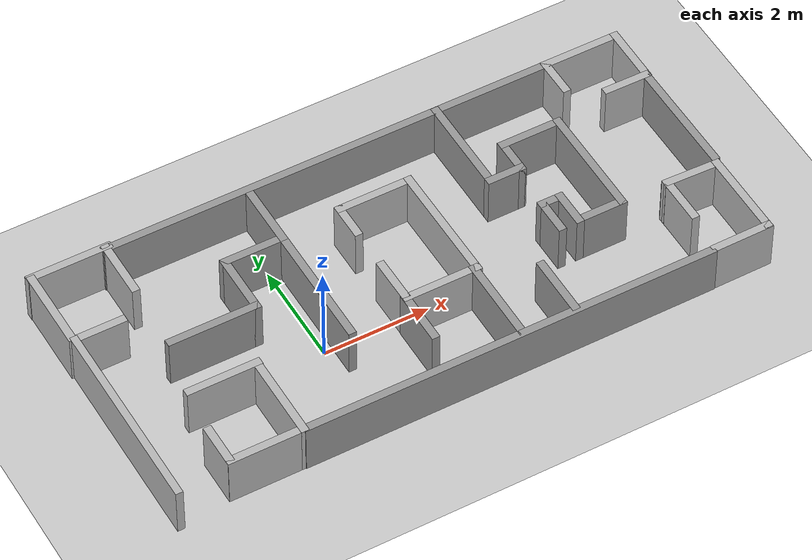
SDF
<sdf version="1.7">
 <world name="default">
  <light name="sun" type="directional">
   <pose>0 0 10 0 -0 0</pose>
   <diffuse>0.8 0.8 0.8 1</diffuse>
   <specular>0.2 0.2 0.2 1</specular>
   <attenuation>
    <range>1000</range>
    <constant>0.9</constant>
    <linear>0.01</linear>
    <quadratic>0.001</quadratic>
   </attenuation>
   <direction>-0.5 0.1 -0.9</direction>
   <spot><inner_angle>0</inner_angle><outer_angle>0</outer_angle><falloff>0</falloff></spot>
  </light>
  <model name="ground_plane">
   <static>1</static>
   <link name="link">
    <collision name="collision">
     <geometry><plane><normal>0 0 1</normal><size>100 100</size></plane></geometry>
     <surface><friction><ode><mu>100</mu><mu2>50</mu2></ode></friction></surface>
    </collision>
    <visual name="visual">
     <cast_shadows>0</cast_shadows>
     <geometry><plane><normal>0 0 1</normal><size>100 100</size></plane></geometry>
     <material>
      <script><uri>file://media/materials/scripts/gazebo.material</uri><name>Gazebo/Grey</name></script>
     </material>
    </visual>
   </link>
  </model>
  <gravity>0 0 -9.8</gravity>
  <magnetic_field>6e-06 2.3e-05 -4.2e-05</magnetic_field>
  <atmosphere type="adiabatic"/>
  <physics name="default_physics" default="0" type="ode">
   <max_step_size>0.001</max_step_size>
   <real_time_factor>1</real_time_factor>
   <real_time_update_rate>1000</real_time_update_rate>
  </physics>
  <scene><ambient>0.4 0.4 0.4 1</ambient><background>0.7 0.7 0.7 1</background><shadows>1</shadows></scene>
  <spherical_coordinates>
   <surface_model>EARTH_WGS84</surface_model>
   <latitude_deg>0</latitude_deg>
   <longitude_deg>0</longitude_deg>
   <elevation>0</elevation>
   <heading_deg>0</heading_deg>
  </spherical_coordinates>
  <model name="final_maze_v2">
   <link name="Wall_13">
    <pose>-5.19174 0.988606 0 0 -0 0</pose>
    <visual name="Wall_13_Visual">
     <pose>0 0 0.5 0 -0 0</pose>
     <geometry><box><size>1 0.15 1</size></box></geometry>
     <meta><layer>0</layer></meta>
     <material><shader type="pixel"/></material>
    </visual>
    <collision name="Wall_13_Collision">
     <pose>0 0 0.5 0 -0 0</pose>
     <geometry><box><size>1 0.15 1</size></box></geometry>
     <surface>
      <friction>
       <ode><mu>1</mu><mu2>1</mu2><fdir1>0 0 0</fdir1><slip1>0</slip1><slip2>0</slip2></ode>
       <torsional>
        <coefficient>1</coefficient>
        <patch_radius>0</patch_radius>
        <surface_radius>0</surface_radius>
        <use_patch_radius>1</use_patch_radius>
        <ode><slip>0</slip></ode>
       </torsional>
      </friction>
      <bounce><restitution_coefficient>0</restitution_coefficient><threshold>1e+06</threshold></bounce>
      <contact>
       <collide_without_contact>0</collide_without_contact>
       <collide_without_contact_bitmask>1</collide_without_contact_bitmask>
       <collide_bitmask>1</collide_bitmask>
       <ode>
        <soft_cfm>0</soft_cfm>
        <soft_erp>0.2</soft_erp>
        <kp>1e+13</kp>
        <kd>1</kd>
        <max_vel>0.01</max_vel>
        <min_depth>0</min_depth>
       </ode>
       <bullet>
        <split_impulse>1</split_impulse>
        <split_impulse_penetration_threshold>-0.01</split_impulse_penetration_threshold>
        <soft_cfm>0</soft_cfm>
        <soft_erp>0.2</soft_erp>
        <kp>1e+13</kp>
        <kd>1</kd>
       </bullet>
      </contact>
     </surface>
    </collision>
   </link>
   <link name="Wall_15">
    <pose>-4.27719 2.00796 0 0 0 -1.5708</pose>
    <inertial>
     <inertia><ixx>0</ixx><ixy>0</ixy><ixz>0</ixz><iyy>0</iyy><iyz>0</iyz><izz>0</izz></inertia>
     <mass>0</mass>
    </inertial>
    <visual name="Wall_15_Visual">
     <pose>0 0 0.5 0 -0 0</pose>
     <geometry><box><size>1.16992 0.15 1</size></box></geometry>
     <meta><layer>0</layer></meta>
     <material><shader type="pixel"/></material>
    </visual>
    <collision name="Wall_15_Collision">
     <pose>0 0 0.5 0 -0 0</pose>
     <geometry><box><size>1.16992 0.15 1</size></box></geometry>
     <surface>
      <friction>
       <ode><mu>1</mu><mu2>1</mu2><fdir1>0 0 0</fdir1><slip1>0</slip1><slip2>0</slip2></ode>
       <torsional>
        <coefficient>1</coefficient>
        <patch_radius>0</patch_radius>
        <surface_radius>0</surface_radius>
        <use_patch_radius>1</use_patch_radius>
        <ode><slip>0</slip></ode>
       </torsional>
      </friction>
      <bounce><restitution_coefficient>0</restitution_coefficient><threshold>1e+06</threshold></bounce>
      <contact>
       <collide_without_contact>0</collide_without_contact>
       <collide_without_contact_bitmask>1</collide_without_contact_bitmask>
       <collide_bitmask>1</collide_bitmask>
       <ode>
        <soft_cfm>0</soft_cfm>
        <soft_erp>0.2</soft_erp>
        <kp>1e+13</kp>
        <kd>1</kd>
        <max_vel>0.01</max_vel>
        <min_depth>0</min_depth>
       </ode>
       <bullet>
        <split_impulse>1</split_impulse>
        <split_impulse_penetration_threshold>-0.01</split_impulse_penetration_threshold>
        <soft_cfm>0</soft_cfm>
        <soft_erp>0.2</soft_erp>
        <kp>1e+13</kp>
        <kd>1</kd>
       </bullet>
      </contact>
     </surface>
    </collision>
   </link>
   <link name="Wall_17">
    <pose>-3.26274 -1.72039 0 0 -0 1.5708</pose>
    <visual name="Wall_17_Visual">
     <pose>0 0 0.5 0 -0 0</pose>
     <geometry><box><size>1.75 0.15 1</size></box></geometry>
     <meta><layer>0</layer></meta>
     <material><shader type="pixel"/></material>
    </visual>
    <collision name="Wall_17_Collision">
     <pose>0 0 0.5 0 -0 0</pose>
     <geometry><box><size>1.75 0.15 1</size></box></geometry>
     <surface>
      <friction>
       <ode><mu>1</mu><mu2>1</mu2><fdir1>0 0 0</fdir1><slip1>0</slip1><slip2>0</slip2></ode>
       <torsional>
        <coefficient>1</coefficient>
        <patch_radius>0</patch_radius>
        <surface_radius>0</surface_radius>
        <use_patch_radius>1</use_patch_radius>
        <ode><slip>0</slip></ode>
       </torsional>
      </friction>
      <bounce><restitution_coefficient>0</restitution_coefficient><threshold>1e+06</threshold></bounce>
      <contact>
       <collide_without_contact>0</collide_without_contact>
       <collide_without_contact_bitmask>1</collide_without_contact_bitmask>
       <collide_bitmask>1</collide_bitmask>
       <ode>
        <soft_cfm>0</soft_cfm>
        <soft_erp>0.2</soft_erp>
        <kp>1e+13</kp>
        <kd>1</kd>
        <max_vel>0.01</max_vel>
        <min_depth>0</min_depth>
       </ode>
       <bullet>
        <split_impulse>1</split_impulse>
        <split_impulse_penetration_threshold>-0.01</split_impulse_penetration_threshold>
        <soft_cfm>0</soft_cfm>
        <soft_erp>0.2</soft_erp>
        <kp>1e+13</kp>
        <kd>1</kd>
       </bullet>
      </contact>
     </surface>
    </collision>
   </link>
   <link name="Wall_17_clone">
    <pose>-4.61531 -2.15743 0 0 -0 1.5708</pose>
    <inertial>
     <inertia><ixx>0</ixx><ixy>0</ixy><ixz>0</ixz><iyy>0</iyy><iyz>0</iyz><izz>0</izz></inertia>
     <mass>0</mass>
    </inertial>
    <visual name="Wall_17_Visual">
     <pose>0 0 0.5 0 -0 0</pose>
     <geometry><box><size>0.870384 0.15 1</size></box></geometry>
     <meta><layer>0</layer></meta>
     <material><shader type="pixel"/></material>
    </visual>
    <collision name="Wall_17_Collision">
     <pose>0 0 0.5 0 -0 0</pose>
     <geometry><box><size>0.870384 0.15 1</size></box></geometry>
     <surface>
      <friction>
       <ode><mu>1</mu><mu2>1</mu2><fdir1>0 0 0</fdir1><slip1>0</slip1><slip2>0</slip2></ode>
       <torsional>
        <coefficient>1</coefficient>
        <patch_radius>0</patch_radius>
        <surface_radius>0</surface_radius>
        <use_patch_radius>1</use_patch_radius>
        <ode><slip>0</slip></ode>
       </torsional>
      </friction>
      <bounce><restitution_coefficient>0</restitution_coefficient><threshold>1e+06</threshold></bounce>
      <contact>
       <collide_without_contact>0</collide_without_contact>
       <collide_without_contact_bitmask>1</collide_without_contact_bitmask>
       <collide_bitmask>1</collide_bitmask>
       <ode>
        <soft_cfm>0</soft_cfm>
        <soft_erp>0.2</soft_erp>
        <kp>1e+13</kp>
        <kd>1</kd>
        <max_vel>0.01</max_vel>
        <min_depth>0</min_depth>
       </ode>
       <bullet>
        <split_impulse>1</split_impulse>
        <split_impulse_penetration_threshold>-0.01</split_impulse_penetration_threshold>
        <soft_cfm>0</soft_cfm>
        <soft_erp>0.2</soft_erp>
        <kp>1e+13</kp>
        <kd>1</kd>
       </bullet>
      </contact>
     </surface>
    </collision>
   </link>
   <link name="Wall_18">
    <pose>-3.88391 -0.920394 0 0 -0 3.14159</pose>
    <inertial>
     <inertia><ixx>0</ixx><ixy>0</ixy><ixz>0</ixz><iyy>0</iyy><iyz>0</iyz><izz>0</izz></inertia>
     <mass>0</mass>
    </inertial>
    <visual name="Wall_18_Visual">
     <pose>0 0 0.5 0 -0 0</pose>
     <geometry><box><size>1.41475 0.15 1</size></box></geometry>
     <meta><layer>0</layer></meta>
     <material><shader type="pixel"/></material>
    </visual>
    <collision name="Wall_18_Collision">
     <pose>0 0 0.5 0 -0 0</pose>
     <geometry><box><size>1.41475 0.15 1</size></box></geometry>
     <surface>
      <friction>
       <ode><mu>1</mu><mu2>1</mu2><fdir1>0 0 0</fdir1><slip1>0</slip1><slip2>0</slip2></ode>
       <torsional>
        <coefficient>1</coefficient>
        <patch_radius>0</patch_radius>
        <surface_radius>0</surface_radius>
        <use_patch_radius>1</use_patch_radius>
        <ode><slip>0</slip></ode>
       </torsional>
      </friction>
      <bounce><restitution_coefficient>0</restitution_coefficient><threshold>1e+06</threshold></bounce>
      <contact>
       <collide_without_contact>0</collide_without_contact>
       <collide_without_contact_bitmask>1</collide_without_contact_bitmask>
       <collide_bitmask>1</collide_bitmask>
       <ode>
        <soft_cfm>0</soft_cfm>
        <soft_erp>0.2</soft_erp>
        <kp>1e+13</kp>
        <kd>1</kd>
        <max_vel>0.01</max_vel>
        <min_depth>0</min_depth>
       </ode>
       <bullet>
        <split_impulse>1</split_impulse>
        <split_impulse_penetration_threshold>-0.01</split_impulse_penetration_threshold>
        <soft_cfm>0</soft_cfm>
        <soft_erp>0.2</soft_erp>
        <kp>1e+13</kp>
        <kd>1</kd>
       </bullet>
      </contact>
     </surface>
    </collision>
   </link>
   <link name="Wall_20">
    <pose>-3.48874 0.163606 0 0 -0 0</pose>
    <visual name="Wall_20_Visual">
     <pose>0 0 0.5 0 -0 0</pose>
     <geometry><box><size>1.75 0.15 1</size></box></geometry>
     <material>
      <script><uri>file://media/materials/scripts/gazebo.material</uri><name>Gazebo/Grey</name></script>
      <ambient>1 1 1 1</ambient>
      <shader type="pixel"/>
     </material>
     <meta><layer>0</layer></meta>
    </visual>
    <collision name="Wall_20_Collision">
     <pose>0 0 0.5 0 -0 0</pose>
     <geometry><box><size>1.75 0.15 1</size></box></geometry>
     <surface>
      <friction>
       <ode><mu>1</mu><mu2>1</mu2><fdir1>0 0 0</fdir1><slip1>0</slip1><slip2>0</slip2></ode>
       <torsional>
        <coefficient>1</coefficient>
        <patch_radius>0</patch_radius>
        <surface_radius>0</surface_radius>
        <use_patch_radius>1</use_patch_radius>
        <ode><slip>0</slip></ode>
       </torsional>
      </friction>
      <bounce><restitution_coefficient>0</restitution_coefficient><threshold>1e+06</threshold></bounce>
      <contact>
       <collide_without_contact>0</collide_without_contact>
       <collide_without_contact_bitmask>1</collide_without_contact_bitmask>
       <collide_bitmask>1</collide_bitmask>
       <ode>
        <soft_cfm>0</soft_cfm>
        <soft_erp>0.2</soft_erp>
        <kp>1e+13</kp>
        <kd>1</kd>
        <max_vel>0.01</max_vel>
        <min_depth>0</min_depth>
       </ode>
       <bullet>
        <split_impulse>1</split_impulse>
        <split_impulse_penetration_threshold>-0.01</split_impulse_penetration_threshold>
        <soft_cfm>0</soft_cfm>
        <soft_erp>0.2</soft_erp>
        <kp>1e+13</kp>
        <kd>1</kd>
       </bullet>
      </contact>
     </surface>
    </collision>
   </link>
   <link name="Wall_21">
    <pose>-2.68873 0.713606 0 0 -0 1.5708</pose>
    <visual name="Wall_21_Visual">
     <pose>0 0 0.5 0 -0 0</pose>
     <geometry><box><size>1.25 0.15 1</size></box></geometry>
     <material>
      <script><uri>file://media/materials/scripts/gazebo.material</uri><name>Gazebo/Grey</name></script>
      <ambient>1 1 1 1</ambient>
      <shader type="pixel"/>
     </material>
     <meta><layer>0</layer></meta>
    </visual>
    <collision name="Wall_21_Collision">
     <pose>0 0 0.5 0 -0 0</pose>
     <geometry><box><size>1.25 0.15 1</size></box></geometry>
     <surface>
      <friction>
       <ode><mu>1</mu><mu2>1</mu2><fdir1>0 0 0</fdir1><slip1>0</slip1><slip2>0</slip2></ode>
       <torsional>
        <coefficient>1</coefficient>
        <patch_radius>0</patch_radius>
        <surface_radius>0</surface_radius>
        <use_patch_radius>1</use_patch_radius>
        <ode><slip>0</slip></ode>
       </torsional>
      </friction>
      <bounce><restitution_coefficient>0</restitution_coefficient><threshold>1e+06</threshold></bounce>
      <contact>
       <collide_without_contact>0</collide_without_contact>
       <collide_without_contact_bitmask>1</collide_without_contact_bitmask>
       <collide_bitmask>1</collide_bitmask>
       <ode>
        <soft_cfm>0</soft_cfm>
        <soft_erp>0.2</soft_erp>
        <kp>1e+13</kp>
        <kd>1</kd>
        <max_vel>0.01</max_vel>
        <min_depth>0</min_depth>
       </ode>
       <bullet>
        <split_impulse>1</split_impulse>
        <split_impulse_penetration_threshold>-0.01</split_impulse_penetration_threshold>
        <soft_cfm>0</soft_cfm>
        <soft_erp>0.2</soft_erp>
        <kp>1e+13</kp>
        <kd>1</kd>
       </bullet>
      </contact>
     </surface>
    </collision>
   </link>
   <link name="Wall_22">
    <pose>-2.13874 1.26361 0 0 -0 0</pose>
    <visual name="Wall_22_Visual">
     <pose>0 0 0.5 0 -0 0</pose>
     <geometry><box><size>1.25 0.15 1</size></box></geometry>
     <material>
      <script><uri>file://media/materials/scripts/gazebo.material</uri><name>Gazebo/Grey</name></script>
      <ambient>1 1 1 1</ambient>
      <shader type="pixel"/>
     </material>
     <meta><layer>0</layer></meta>
    </visual>
    <collision name="Wall_22_Collision">
     <pose>0 0 0.5 0 -0 0</pose>
     <geometry><box><size>1.25 0.15 1</size></box></geometry>
     <surface>
      <friction>
       <ode><mu>1</mu><mu2>1</mu2><fdir1>0 0 0</fdir1><slip1>0</slip1><slip2>0</slip2></ode>
       <torsional>
        <coefficient>1</coefficient>
        <patch_radius>0</patch_radius>
        <surface_radius>0</surface_radius>
        <use_patch_radius>1</use_patch_radius>
        <ode><slip>0</slip></ode>
       </torsional>
      </friction>
      <bounce><restitution_coefficient>0</restitution_coefficient><threshold>1e+06</threshold></bounce>
      <contact>
       <collide_without_contact>0</collide_without_contact>
       <collide_without_contact_bitmask>1</collide_without_contact_bitmask>
       <collide_bitmask>1</collide_bitmask>
       <ode>
        <soft_cfm>0</soft_cfm>
        <soft_erp>0.2</soft_erp>
        <kp>1e+13</kp>
        <kd>1</kd>
        <max_vel>0.01</max_vel>
        <min_depth>0</min_depth>
       </ode>
       <bullet>
        <split_impulse>1</split_impulse>
        <split_impulse_penetration_threshold>-0.01</split_impulse_penetration_threshold>
        <soft_cfm>0</soft_cfm>
        <soft_erp>0.2</soft_erp>
        <kp>1e+13</kp>
        <kd>1</kd>
       </bullet>
      </contact>
     </surface>
    </collision>
   </link>
   <link name="Wall_23">
    <pose>-1.58874 1.81361 0 0 -0 1.5708</pose>
    <visual name="Wall_23_Visual">
     <pose>0 0 0.5 0 -0 0</pose>
     <geometry><box><size>1.25 0.15 1</size></box></geometry>
     <material>
      <script><uri>file://media/materials/scripts/gazebo.material</uri><name>Gazebo/Grey</name></script>
      <ambient>1 1 1 1</ambient>
      <shader type="pixel"/>
     </material>
     <meta><layer>0</layer></meta>
    </visual>
    <collision name="Wall_23_Collision">
     <pose>0 0 0.5 0 -0 0</pose>
     <geometry><box><size>1.25 0.15 1</size></box></geometry>
     <surface>
      <friction>
       <ode><mu>1</mu><mu2>1</mu2><fdir1>0 0 0</fdir1><slip1>0</slip1><slip2>0</slip2></ode>
       <torsional>
        <coefficient>1</coefficient>
        <patch_radius>0</patch_radius>
        <surface_radius>0</surface_radius>
        <use_patch_radius>1</use_patch_radius>
        <ode><slip>0</slip></ode>
       </torsional>
      </friction>
      <bounce><restitution_coefficient>0</restitution_coefficient><threshold>1e+06</threshold></bounce>
      <contact>
       <collide_without_contact>0</collide_without_contact>
       <collide_without_contact_bitmask>1</collide_without_contact_bitmask>
       <collide_bitmask>1</collide_bitmask>
       <ode>
        <soft_cfm>0</soft_cfm>
        <soft_erp>0.2</soft_erp>
        <kp>1e+13</kp>
        <kd>1</kd>
        <max_vel>0.01</max_vel>
        <min_depth>0</min_depth>
       </ode>
       <bullet>
        <split_impulse>1</split_impulse>
        <split_impulse_penetration_threshold>-0.01</split_impulse_penetration_threshold>
        <soft_cfm>0</soft_cfm>
        <soft_erp>0.2</soft_erp>
        <kp>1e+13</kp>
        <kd>1</kd>
       </bullet>
      </contact>
     </surface>
    </collision>
   </link>
   <link name="Wall_25">
    <pose>-1.58874 0.088606 0 0 0 -1.5708</pose>
    <visual name="Wall_25_Visual">
     <pose>0 0 0.5 0 -0 0</pose>
     <geometry><box><size>2.5 0.15 1</size></box></geometry>
     <material>
      <script><uri>file://media/materials/scripts/gazebo.material</uri><name>Gazebo/Grey</name></script>
      <ambient>1 1 1 1</ambient>
      <shader type="pixel"/>
     </material>
     <meta><layer>0</layer></meta>
    </visual>
    <collision name="Wall_25_Collision">
     <pose>0 0 0.5 0 -0 0</pose>
     <geometry><box><size>2.5 0.15 1</size></box></geometry>
     <surface>
      <friction>
       <ode><mu>1</mu><mu2>1</mu2><fdir1>0 0 0</fdir1><slip1>0</slip1><slip2>0</slip2></ode>
       <torsional>
        <coefficient>1</coefficient>
        <patch_radius>0</patch_radius>
        <surface_radius>0</surface_radius>
        <use_patch_radius>1</use_patch_radius>
        <ode><slip>0</slip></ode>
       </torsional>
      </friction>
      <bounce><restitution_coefficient>0</restitution_coefficient><threshold>1e+06</threshold></bounce>
      <contact>
       <collide_without_contact>0</collide_without_contact>
       <collide_without_contact_bitmask>1</collide_without_contact_bitmask>
       <collide_bitmask>1</collide_bitmask>
       <ode>
        <soft_cfm>0</soft_cfm>
        <soft_erp>0.2</soft_erp>
        <kp>1e+13</kp>
        <kd>1</kd>
        <max_vel>0.01</max_vel>
        <min_depth>0</min_depth>
       </ode>
       <bullet>
        <split_impulse>1</split_impulse>
        <split_impulse_penetration_threshold>-0.01</split_impulse_penetration_threshold>
        <soft_cfm>0</soft_cfm>
        <soft_erp>0.2</soft_erp>
        <kp>1e+13</kp>
        <kd>1</kd>
       </bullet>
      </contact>
     </surface>
    </collision>
   </link>
   <link name="Wall_27">
    <pose>-0.439735 1.04861 0 0 -0 1.5708</pose>
    <visual name="Wall_27_Visual">
     <pose>0 0 0.5 0 -0 0</pose>
     <geometry><box><size>0.75 0.15 1</size></box></geometry>
     <meta><layer>0</layer></meta>
     <material><shader type="pixel"/></material>
    </visual>
    <collision name="Wall_27_Collision">
     <pose>0 0 0.5 0 -0 0</pose>
     <geometry><box><size>0.75 0.15 1</size></box></geometry>
     <surface>
      <friction>
       <ode><mu>1</mu><mu2>1</mu2><fdir1>0 0 0</fdir1><slip1>0</slip1><slip2>0</slip2></ode>
       <torsional>
        <coefficient>1</coefficient>
        <patch_radius>0</patch_radius>
        <surface_radius>0</surface_radius>
        <use_patch_radius>1</use_patch_radius>
        <ode><slip>0</slip></ode>
       </torsional>
      </friction>
      <bounce><restitution_coefficient>0</restitution_coefficient><threshold>1e+06</threshold></bounce>
      <contact>
       <collide_without_contact>0</collide_without_contact>
       <collide_without_contact_bitmask>1</collide_without_contact_bitmask>
       <collide_bitmask>1</collide_bitmask>
       <ode>
        <soft_cfm>0</soft_cfm>
        <soft_erp>0.2</soft_erp>
        <kp>1e+13</kp>
        <kd>1</kd>
        <max_vel>0.01</max_vel>
        <min_depth>0</min_depth>
       </ode>
       <bullet>
        <split_impulse>1</split_impulse>
        <split_impulse_penetration_threshold>-0.01</split_impulse_penetration_threshold>
        <soft_cfm>0</soft_cfm>
        <soft_erp>0.2</soft_erp>
        <kp>1e+13</kp>
        <kd>1</kd>
       </bullet>
      </contact>
     </surface>
    </collision>
   </link>
   <link name="Wall_28">
    <pose>0.235265 1.34861 0 0 -0 0</pose>
    <visual name="Wall_28_Visual">
     <pose>0 0 0.5 0 -0 0</pose>
     <geometry><box><size>1.5 0.15 1</size></box></geometry>
     <meta><layer>0</layer></meta>
     <material><shader type="pixel"/></material>
    </visual>
    <collision name="Wall_28_Collision">
     <pose>0 0 0.5 0 -0 0</pose>
     <geometry><box><size>1.5 0.15 1</size></box></geometry>
     <surface>
      <friction>
       <ode><mu>1</mu><mu2>1</mu2><fdir1>0 0 0</fdir1><slip1>0</slip1><slip2>0</slip2></ode>
       <torsional>
        <coefficient>1</coefficient>
        <patch_radius>0</patch_radius>
        <surface_radius>0</surface_radius>
        <use_patch_radius>1</use_patch_radius>
        <ode><slip>0</slip></ode>
       </torsional>
      </friction>
      <bounce><restitution_coefficient>0</restitution_coefficient><threshold>1e+06</threshold></bounce>
      <contact>
       <collide_without_contact>0</collide_without_contact>
       <collide_without_contact_bitmask>1</collide_without_contact_bitmask>
       <collide_bitmask>1</collide_bitmask>
       <ode>
        <soft_cfm>0</soft_cfm>
        <soft_erp>0.2</soft_erp>
        <kp>1e+13</kp>
        <kd>1</kd>
        <max_vel>0.01</max_vel>
        <min_depth>0</min_depth>
       </ode>
       <bullet>
        <split_impulse>1</split_impulse>
        <split_impulse_penetration_threshold>-0.01</split_impulse_penetration_threshold>
        <soft_cfm>0</soft_cfm>
        <soft_erp>0.2</soft_erp>
        <kp>1e+13</kp>
        <kd>1</kd>
       </bullet>
      </contact>
     </surface>
    </collision>
   </link>
   <link name="Wall_29">
    <pose>0.877343 -1.70359 0 0 0 -1.5708</pose>
    <inertial>
     <inertia><ixx>0</ixx><ixy>0</ixy><ixz>0</ixz><iyy>0</iyy><iyz>0</iyz><izz>0</izz></inertia>
     <mass>0</mass>
    </inertial>
    <visual name="Wall_29_Visual">
     <pose>0 0 0.5 0 -0 0</pose>
     <geometry><box><size>1.71998 0.15 1</size></box></geometry>
     <material>
      <script><uri>file://media/materials/scripts/gazebo.material</uri><name>Gazebo/Grey</name></script>
      <ambient>1 1 1 1</ambient>
      <shader type="pixel"/>
     </material>
     <meta><layer>0</layer></meta>
    </visual>
    <collision name="Wall_29_Collision">
     <pose>0 0 0.5 0 -0 0</pose>
     <geometry><box><size>1.71998 0.15 1</size></box></geometry>
     <surface>
      <friction>
       <ode><mu>1</mu><mu2>1</mu2><fdir1>0 0 0</fdir1><slip1>0</slip1><slip2>0</slip2></ode>
       <torsional>
        <coefficient>1</coefficient>
        <patch_radius>0</patch_radius>
        <surface_radius>0</surface_radius>
        <use_patch_radius>1</use_patch_radius>
        <ode><slip>0</slip></ode>
       </torsional>
      </friction>
      <bounce><restitution_coefficient>0</restitution_coefficient><threshold>1e+06</threshold></bounce>
      <contact>
       <collide_without_contact>0</collide_without_contact>
       <collide_without_contact_bitmask>1</collide_without_contact_bitmask>
       <collide_bitmask>1</collide_bitmask>
       <ode>
        <soft_cfm>0</soft_cfm>
        <soft_erp>0.2</soft_erp>
        <kp>1e+13</kp>
        <kd>1</kd>
        <max_vel>0.01</max_vel>
        <min_depth>0</min_depth>
       </ode>
       <bullet>
        <split_impulse>1</split_impulse>
        <split_impulse_penetration_threshold>-0.01</split_impulse_penetration_threshold>
        <soft_cfm>0</soft_cfm>
        <soft_erp>0.2</soft_erp>
        <kp>1e+13</kp>
        <kd>1</kd>
       </bullet>
      </contact>
     </surface>
    </collision>
   </link>
   <link name="Wall_29_clone">
    <pose>1.90614 -1.93473 0 0 0 -1.5708</pose>
    <inertial>
     <inertia><ixx>0</ixx><ixy>0</ixy><ixz>0</ixz><iyy>0</iyy><iyz>0</iyz><izz>0</izz></inertia>
     <mass>0</mass>
    </inertial>
    <visual name="Wall_29_Visual">
     <pose>0 0 0.5 0 -0 0</pose>
     <geometry><box><size>1.20691 0.15 1</size></box></geometry>
     <material>
      <script><uri>file://media/materials/scripts/gazebo.material</uri><name>Gazebo/Grey</name></script>
      <ambient>1 1 1 1</ambient>
      <shader type="pixel"/>
     </material>
     <meta><layer>0</layer></meta>
    </visual>
    <collision name="Wall_29_Collision">
     <pose>0 0 0.5 0 -0 0</pose>
     <geometry><box><size>1.20691 0.15 1</size></box></geometry>
     <surface>
      <friction>
       <ode><mu>1</mu><mu2>1</mu2><fdir1>0 0 0</fdir1><slip1>0</slip1><slip2>0</slip2></ode>
       <torsional>
        <coefficient>1</coefficient>
        <patch_radius>0</patch_radius>
        <surface_radius>0</surface_radius>
        <use_patch_radius>1</use_patch_radius>
        <ode><slip>0</slip></ode>
       </torsional>
      </friction>
      <bounce><restitution_coefficient>0</restitution_coefficient><threshold>1e+06</threshold></bounce>
      <contact>
       <collide_without_contact>0</collide_without_contact>
       <collide_without_contact_bitmask>1</collide_without_contact_bitmask>
       <collide_bitmask>1</collide_bitmask>
       <ode>
        <soft_cfm>0</soft_cfm>
        <soft_erp>0.2</soft_erp>
        <kp>1e+13</kp>
        <kd>1</kd>
        <max_vel>0.01</max_vel>
        <min_depth>0</min_depth>
       </ode>
       <bullet>
        <split_impulse>1</split_impulse>
        <split_impulse_penetration_threshold>-0.01</split_impulse_penetration_threshold>
        <soft_cfm>0</soft_cfm>
        <soft_erp>0.2</soft_erp>
        <kp>1e+13</kp>
        <kd>1</kd>
       </bullet>
      </contact>
     </surface>
    </collision>
   </link>
   <link name="Wall_3">
    <pose>0.673122 -2.53429 0 0 -0 0</pose>
    <inertial>
     <inertia><ixx>0</ixx><ixy>0</ixy><ixz>0</ixz><iyy>0</iyy><iyz>0</iyz><izz>0</izz></inertia>
     <mass>0</mass>
    </inertial>
    <visual name="Wall_3_Visual">
     <pose>0 0 0.5 0 -0 0</pose>
     <geometry><box><size>7.88308 0.15 1</size></box></geometry>
     <material>
      <script><uri>file://media/materials/scripts/gazebo.material</uri><name>Gazebo/Grey</name></script>
      <ambient>1 1 1 1</ambient>
      <shader type="pixel"/>
     </material>
     <meta><layer>0</layer></meta>
    </visual>
    <collision name="Wall_3_Collision">
     <pose>0 0 0.5 0 -0 0</pose>
     <geometry><box><size>7.88308 0.15 1</size></box></geometry>
     <surface>
      <friction>
       <ode><mu>1</mu><mu2>1</mu2><fdir1>0 0 0</fdir1><slip1>0</slip1><slip2>0</slip2></ode>
       <torsional>
        <coefficient>1</coefficient>
        <patch_radius>0</patch_radius>
        <surface_radius>0</surface_radius>
        <use_patch_radius>1</use_patch_radius>
        <ode><slip>0</slip></ode>
       </torsional>
      </friction>
      <bounce><restitution_coefficient>0</restitution_coefficient><threshold>1e+06</threshold></bounce>
      <contact>
       <collide_without_contact>0</collide_without_contact>
       <collide_without_contact_bitmask>1</collide_without_contact_bitmask>
       <collide_bitmask>1</collide_bitmask>
       <ode>
        <soft_cfm>0</soft_cfm>
        <soft_erp>0.2</soft_erp>
        <kp>1e+13</kp>
        <kd>1</kd>
        <max_vel>0.01</max_vel>
        <min_depth>0</min_depth>
       </ode>
       <bullet>
        <split_impulse>1</split_impulse>
        <split_impulse_penetration_threshold>-0.01</split_impulse_penetration_threshold>
        <soft_cfm>0</soft_cfm>
        <soft_erp>0.2</soft_erp>
        <kp>1e+13</kp>
        <kd>1</kd>
       </bullet>
      </contact>
     </surface>
    </collision>
   </link>
   <link name="Wall_31">
    <pose>0.250265 -0.917394 0 0 -0 3.14159</pose>
    <visual name="Wall_31_Visual">
     <pose>0 0 0.5 0 -0 0</pose>
     <geometry><box><size>1.5 0.15 1</size></box></geometry>
     <meta><layer>0</layer></meta>
     <material><shader type="pixel"/></material>
    </visual>
    <collision name="Wall_31_Collision">
     <pose>0 0 0.5 0 -0 0</pose>
     <geometry><box><size>1.5 0.15 1</size></box></geometry>
     <surface>
      <friction>
       <ode><mu>1</mu><mu2>1</mu2><fdir1>0 0 0</fdir1><slip1>0</slip1><slip2>0</slip2></ode>
       <torsional>
        <coefficient>1</coefficient>
        <patch_radius>0</patch_radius>
        <surface_radius>0</surface_radius>
        <use_patch_radius>1</use_patch_radius>
        <ode><slip>0</slip></ode>
       </torsional>
      </friction>
      <bounce><restitution_coefficient>0</restitution_coefficient><threshold>1e+06</threshold></bounce>
      <contact>
       <collide_without_contact>0</collide_without_contact>
       <collide_without_contact_bitmask>1</collide_without_contact_bitmask>
       <collide_bitmask>1</collide_bitmask>
       <ode>
        <soft_cfm>0</soft_cfm>
        <soft_erp>0.2</soft_erp>
        <kp>1e+13</kp>
        <kd>1</kd>
        <max_vel>0.01</max_vel>
        <min_depth>0</min_depth>
       </ode>
       <bullet>
        <split_impulse>1</split_impulse>
        <split_impulse_penetration_threshold>-0.01</split_impulse_penetration_threshold>
        <soft_cfm>0</soft_cfm>
        <soft_erp>0.2</soft_erp>
        <kp>1e+13</kp>
        <kd>1</kd>
       </bullet>
      </contact>
     </surface>
    </collision>
   </link>
   <link name="Wall_33">
    <pose>-0.433794 -1.38953 0 0 0 -1.5708</pose>
    <inertial>
     <inertia><ixx>0</ixx><ixy>0</ixy><ixz>0</ixz><iyy>0</iyy><iyz>0</iyz><izz>0</izz></inertia>
     <mass>0</mass>
    </inertial>
    <visual name="Wall_33_Visual">
     <pose>0 0 0.5 0 -0 0</pose>
     <geometry><box><size>1.07217 0.15 1</size></box></geometry>
     <material>
      <script><uri>file://media/materials/scripts/gazebo.material</uri><name>Gazebo/Grey</name></script>
      <ambient>1 1 1 1</ambient>
      <shader type="pixel"/>
     </material>
     <meta><layer>0</layer></meta>
    </visual>
    <collision name="Wall_33_Collision">
     <pose>0 0 0.5 0 -0 0</pose>
     <geometry><box><size>1.07217 0.15 1</size></box></geometry>
     <surface>
      <friction>
       <ode><mu>1</mu><mu2>1</mu2><fdir1>0 0 0</fdir1><slip1>0</slip1><slip2>0</slip2></ode>
       <torsional>
        <coefficient>1</coefficient>
        <patch_radius>0</patch_radius>
        <surface_radius>0</surface_radius>
        <use_patch_radius>1</use_patch_radius>
        <ode><slip>0</slip></ode>
       </torsional>
      </friction>
      <bounce><restitution_coefficient>0</restitution_coefficient><threshold>1e+06</threshold></bounce>
      <contact>
       <collide_without_contact>0</collide_without_contact>
       <collide_without_contact_bitmask>1</collide_without_contact_bitmask>
       <collide_bitmask>1</collide_bitmask>
       <ode>
        <soft_cfm>0</soft_cfm>
        <soft_erp>0.2</soft_erp>
        <kp>1e+13</kp>
        <kd>1</kd>
        <max_vel>0.01</max_vel>
        <min_depth>0</min_depth>
       </ode>
       <bullet>
        <split_impulse>1</split_impulse>
        <split_impulse_penetration_threshold>-0.01</split_impulse_penetration_threshold>
        <soft_cfm>0</soft_cfm>
        <soft_erp>0.2</soft_erp>
        <kp>1e+13</kp>
        <kd>1</kd>
       </bullet>
      </contact>
     </surface>
    </collision>
   </link>
   <link name="Wall_39">
    <pose>2.10527 1.58161 0 0 0 -1.5708</pose>
    <visual name="Wall_39_Visual_0">
     <pose>0 0 0.5 0 -0 0</pose>
     <geometry><box><size>2 0.15 1</size></box></geometry>
     <material>
      <script><uri>file://media/materials/scripts/gazebo.material</uri><name>Gazebo/Grey</name></script>
      <ambient>1 1 1 1</ambient>
      <shader type="pixel"/>
     </material>
     <meta><layer>0</layer></meta>
    </visual>
    <collision name="Wall_39_Collision_0">
     <pose>0 0 0.5 0 -0 0</pose>
     <geometry><box><size>2 0.15 1</size></box></geometry>
     <surface>
      <friction>
       <ode><mu>1</mu><mu2>1</mu2><fdir1>0 0 0</fdir1><slip1>0</slip1><slip2>0</slip2></ode>
       <torsional>
        <coefficient>1</coefficient>
        <patch_radius>0</patch_radius>
        <surface_radius>0</surface_radius>
        <use_patch_radius>1</use_patch_radius>
        <ode><slip>0</slip></ode>
       </torsional>
      </friction>
      <bounce><restitution_coefficient>0</restitution_coefficient><threshold>1e+06</threshold></bounce>
      <contact>
       <collide_without_contact>0</collide_without_contact>
       <collide_without_contact_bitmask>1</collide_without_contact_bitmask>
       <collide_bitmask>1</collide_bitmask>
       <ode>
        <soft_cfm>0</soft_cfm>
        <soft_erp>0.2</soft_erp>
        <kp>1e+13</kp>
        <kd>1</kd>
        <max_vel>0.01</max_vel>
        <min_depth>0</min_depth>
       </ode>
       <bullet>
        <split_impulse>1</split_impulse>
        <split_impulse_penetration_threshold>-0.01</split_impulse_penetration_threshold>
        <soft_cfm>0</soft_cfm>
        <soft_erp>0.2</soft_erp>
        <kp>1e+13</kp>
        <kd>1</kd>
       </bullet>
      </contact>
     </surface>
    </collision>
   </link>
   <link name="Wall_40">
    <pose>2.40526 0.656606 0 0 -0 0</pose>
    <inertial>
     <mass>1</mass>
     <inertia><ixx>1</ixx><ixy>0</ixy><ixz>0</ixz><iyy>1</iyy><iyz>0</iyz><izz>1</izz></inertia>
    </inertial>
    <visual name="Wall_40_Visual">
     <pose>0 0 0.5 0 -0 0</pose>
     <geometry><box><size>0.75 0.15 1</size></box></geometry>
     <material>
      <script><uri>file://media/materials/scripts/gazebo.material</uri><name>Gazebo/Grey</name></script>
      <ambient>1 1 1 1</ambient>
      <shader type="pixel"><normal_map>__default__</normal_map></shader>
      <diffuse>0.7 0.7 0.7 1</diffuse>
      <specular>0.01 0.01 0.01 1</specular>
      <emissive>0 0 0 1</emissive>
     </material>
     <meta><layer>0</layer></meta>
    </visual>
    <collision name="Wall_40_Collision">
     <pose>0 0 0.5 0 -0 0</pose>
     <geometry><box><size>0.75 0.15 1</size></box></geometry>
     <surface>
      <friction>
       <ode><mu>1</mu><mu2>1</mu2><fdir1>0 0 0</fdir1><slip1>0</slip1><slip2>0</slip2></ode>
       <torsional>
        <coefficient>1</coefficient>
        <patch_radius>0</patch_radius>
        <surface_radius>0</surface_radius>
        <use_patch_radius>1</use_patch_radius>
        <ode><slip>0</slip></ode>
       </torsional>
      </friction>
      <bounce><restitution_coefficient>0</restitution_coefficient><threshold>1e+06</threshold></bounce>
      <contact>
       <collide_without_contact>0</collide_without_contact>
       <collide_without_contact_bitmask>1</collide_without_contact_bitmask>
       <collide_bitmask>1</collide_bitmask>
       <ode>
        <soft_cfm>0</soft_cfm>
        <soft_erp>0.2</soft_erp>
        <kp>1e+13</kp>
        <kd>1</kd>
        <max_vel>0.01</max_vel>
        <min_depth>0</min_depth>
       </ode>
       <bullet>
        <split_impulse>1</split_impulse>
        <split_impulse_penetration_threshold>-0.01</split_impulse_penetration_threshold>
        <soft_cfm>0</soft_cfm>
        <soft_erp>0.2</soft_erp>
        <kp>1e+13</kp>
        <kd>1</kd>
       </bullet>
      </contact>
     </surface>
    </collision>
   </link>
   <link name="Wall_41">
    <pose>2.70526 0.956606 0 0 -0 1.5708</pose>
    <inertial>
     <mass>1</mass>
     <inertia><ixx>1</ixx><ixy>0</ixy><ixz>0</ixz><iyy>1</iyy><iyz>0</iyz><izz>1</izz></inertia>
    </inertial>
    <visual name="Wall_41_Visual">
     <pose>0 0 0.5 0 -0 0</pose>
     <geometry><box><size>0.75 0.15 1</size></box></geometry>
     <material>
      <script><uri>file://media/materials/scripts/gazebo.material</uri><name>Gazebo/Grey</name></script>
      <ambient>1 1 1 1</ambient>
      <shader type="pixel"><normal_map>__default__</normal_map></shader>
      <diffuse>0.7 0.7 0.7 1</diffuse>
      <specular>0.01 0.01 0.01 1</specular>
      <emissive>0 0 0 1</emissive>
     </material>
     <meta><layer>0</layer></meta>
    </visual>
    <collision name="Wall_41_Collision">
     <pose>0 0 0.5 0 -0 0</pose>
     <geometry><box><size>0.75 0.15 1</size></box></geometry>
     <surface>
      <friction>
       <ode><mu>1</mu><mu2>1</mu2><fdir1>0 0 0</fdir1><slip1>0</slip1><slip2>0</slip2></ode>
       <torsional>
        <coefficient>1</coefficient>
        <patch_radius>0</patch_radius>
        <surface_radius>0</surface_radius>
        <use_patch_radius>1</use_patch_radius>
        <ode><slip>0</slip></ode>
       </torsional>
      </friction>
      <bounce><restitution_coefficient>0</restitution_coefficient><threshold>1e+06</threshold></bounce>
      <contact>
       <collide_without_contact>0</collide_without_contact>
       <collide_without_contact_bitmask>1</collide_without_contact_bitmask>
       <collide_bitmask>1</collide_bitmask>
       <ode>
        <soft_cfm>0</soft_cfm>
        <soft_erp>0.2</soft_erp>
        <kp>1e+13</kp>
        <kd>1</kd>
        <max_vel>0.01</max_vel>
        <min_depth>0</min_depth>
       </ode>
       <bullet>
        <split_impulse>1</split_impulse>
        <split_impulse_penetration_threshold>-0.01</split_impulse_penetration_threshold>
        <soft_cfm>0</soft_cfm>
        <soft_erp>0.2</soft_erp>
        <kp>1e+13</kp>
        <kd>1</kd>
       </bullet>
      </contact>
     </surface>
    </collision>
   </link>
   <link name="Wall_42">
    <pose>3.25527 1.25661 0 0 -0 0</pose>
    <inertial>
     <mass>1</mass>
     <inertia><ixx>1</ixx><ixy>0</ixy><ixz>0</ixz><iyy>1</iyy><iyz>0</iyz><izz>1</izz></inertia>
    </inertial>
    <visual name="Wall_42_Visual">
     <pose>0 0 0.5 0 -0 0</pose>
     <geometry><box><size>1.25 0.15 1</size></box></geometry>
     <material>
      <script><uri>file://media/materials/scripts/gazebo.material</uri><name>Gazebo/Grey</name></script>
      <ambient>1 1 1 1</ambient>
      <shader type="pixel"><normal_map>__default__</normal_map></shader>
      <diffuse>0.7 0.7 0.7 1</diffuse>
      <specular>0.01 0.01 0.01 1</specular>
      <emissive>0 0 0 1</emissive>
     </material>
     <meta><layer>0</layer></meta>
    </visual>
    <collision name="Wall_42_Collision">
     <pose>0 0 0.5 0 -0 0</pose>
     <geometry><box><size>1.25 0.15 1</size></box></geometry>
     <surface>
      <friction>
       <ode><mu>1</mu><mu2>1</mu2><fdir1>0 0 0</fdir1><slip1>0</slip1><slip2>0</slip2></ode>
       <torsional>
        <coefficient>1</coefficient>
        <patch_radius>0</patch_radius>
        <surface_radius>0</surface_radius>
        <use_patch_radius>1</use_patch_radius>
        <ode><slip>0</slip></ode>
       </torsional>
      </friction>
      <bounce><restitution_coefficient>0</restitution_coefficient><threshold>1e+06</threshold></bounce>
      <contact>
       <collide_without_contact>0</collide_without_contact>
       <collide_without_contact_bitmask>1</collide_without_contact_bitmask>
       <collide_bitmask>1</collide_bitmask>
       <ode>
        <soft_cfm>0</soft_cfm>
        <soft_erp>0.2</soft_erp>
        <kp>1e+13</kp>
        <kd>1</kd>
        <max_vel>0.01</max_vel>
        <min_depth>0</min_depth>
       </ode>
       <bullet>
        <split_impulse>1</split_impulse>
        <split_impulse_penetration_threshold>-0.01</split_impulse_penetration_threshold>
        <soft_cfm>0</soft_cfm>
        <soft_erp>0.2</soft_erp>
        <kp>1e+13</kp>
        <kd>1</kd>
       </bullet>
      </contact>
     </surface>
    </collision>
   </link>
   <link name="Wall_43">
    <pose>3.80526 0.206606 0 0 0 -1.5708</pose>
    <inertial>
     <mass>1</mass>
     <inertia><ixx>1</ixx><ixy>0</ixy><ixz>0</ixz><iyy>1</iyy><iyz>0</iyz><izz>1</izz></inertia>
    </inertial>
    <visual name="Wall_43_Visual">
     <pose>0 0 0.5 0 -0 0</pose>
     <geometry><box><size>2.25 0.15 1</size></box></geometry>
     <material>
      <script><uri>file://media/materials/scripts/gazebo.material</uri><name>Gazebo/Grey</name></script>
      <ambient>1 1 1 1</ambient>
      <shader type="pixel"><normal_map>__default__</normal_map></shader>
      <diffuse>0.7 0.7 0.7 1</diffuse>
      <specular>0.01 0.01 0.01 1</specular>
      <emissive>0 0 0 1</emissive>
     </material>
     <meta><layer>0</layer></meta>
    </visual>
    <collision name="Wall_43_Collision">
     <pose>0 0 0.5 0 -0 0</pose>
     <geometry><box><size>2.25 0.15 1</size></box></geometry>
     <surface>
      <friction>
       <ode><mu>1</mu><mu2>1</mu2><fdir1>0 0 0</fdir1><slip1>0</slip1><slip2>0</slip2></ode>
       <torsional>
        <coefficient>1</coefficient>
        <patch_radius>0</patch_radius>
        <surface_radius>0</surface_radius>
        <use_patch_radius>1</use_patch_radius>
        <ode><slip>0</slip></ode>
       </torsional>
      </friction>
      <bounce><restitution_coefficient>0</restitution_coefficient><threshold>1e+06</threshold></bounce>
      <contact>
       <collide_without_contact>0</collide_without_contact>
       <collide_without_contact_bitmask>1</collide_without_contact_bitmask>
       <collide_bitmask>1</collide_bitmask>
       <ode>
        <soft_cfm>0</soft_cfm>
        <soft_erp>0.2</soft_erp>
        <kp>1e+13</kp>
        <kd>1</kd>
        <max_vel>0.01</max_vel>
        <min_depth>0</min_depth>
       </ode>
       <bullet>
        <split_impulse>1</split_impulse>
        <split_impulse_penetration_threshold>-0.01</split_impulse_penetration_threshold>
        <soft_cfm>0</soft_cfm>
        <soft_erp>0.2</soft_erp>
        <kp>1e+13</kp>
        <kd>1</kd>
       </bullet>
      </contact>
     </surface>
    </collision>
   </link>
   <link name="Wall_44">
    <pose>3.38027 -0.843394 0 0 -0 3.14159</pose>
    <inertial>
     <mass>1</mass>
     <inertia><ixx>1</ixx><ixy>0</ixy><ixz>0</ixz><iyy>1</iyy><iyz>0</iyz><izz>1</izz></inertia>
    </inertial>
    <visual name="Wall_44_Visual">
     <pose>0 0 0.5 0 -0 0</pose>
     <geometry><box><size>1 0.15 1</size></box></geometry>
     <material>
      <script><uri>file://media/materials/scripts/gazebo.material</uri><name>Gazebo/Grey</name></script>
      <ambient>1 1 1 1</ambient>
      <shader type="pixel"><normal_map>__default__</normal_map></shader>
      <diffuse>0.7 0.7 0.7 1</diffuse>
      <specular>0.01 0.01 0.01 1</specular>
      <emissive>0 0 0 1</emissive>
     </material>
     <meta><layer>0</layer></meta>
    </visual>
    <collision name="Wall_44_Collision">
     <pose>0 0 0.5 0 -0 0</pose>
     <geometry><box><size>1 0.15 1</size></box></geometry>
     <surface>
      <friction>
       <ode><mu>1</mu><mu2>1</mu2><fdir1>0 0 0</fdir1><slip1>0</slip1><slip2>0</slip2></ode>
       <torsional>
        <coefficient>1</coefficient>
        <patch_radius>0</patch_radius>
        <surface_radius>0</surface_radius>
        <use_patch_radius>1</use_patch_radius>
        <ode><slip>0</slip></ode>
       </torsional>
      </friction>
      <bounce><restitution_coefficient>0</restitution_coefficient><threshold>1e+06</threshold></bounce>
      <contact>
       <collide_without_contact>0</collide_without_contact>
       <collide_without_contact_bitmask>1</collide_without_contact_bitmask>
       <collide_bitmask>1</collide_bitmask>
       <ode>
        <soft_cfm>0</soft_cfm>
        <soft_erp>0.2</soft_erp>
        <kp>1e+13</kp>
        <kd>1</kd>
        <max_vel>0.01</max_vel>
        <min_depth>0</min_depth>
       </ode>
       <bullet>
        <split_impulse>1</split_impulse>
        <split_impulse_penetration_threshold>-0.01</split_impulse_penetration_threshold>
        <soft_cfm>0</soft_cfm>
        <soft_erp>0.2</soft_erp>
        <kp>1e+13</kp>
        <kd>1</kd>
       </bullet>
      </contact>
     </surface>
    </collision>
   </link>
   <link name="Wall_45">
    <pose>2.95526 -0.543394 0 0 -0 1.5708</pose>
    <inertial>
     <mass>1</mass>
     <inertia><ixx>1</ixx><ixy>0</ixy><ixz>0</ixz><iyy>1</iyy><iyz>0</iyz><izz>1</izz></inertia>
    </inertial>
    <visual name="Wall_45_Visual">
     <pose>0 0 0.5 0 -0 0</pose>
     <geometry><box><size>0.75 0.15 1</size></box></geometry>
     <material>
      <script><uri>file://media/materials/scripts/gazebo.material</uri><name>Gazebo/Grey</name></script>
      <ambient>1 1 1 1</ambient>
      <shader type="pixel"><normal_map>__default__</normal_map></shader>
      <diffuse>0.7 0.7 0.7 1</diffuse>
      <specular>0.01 0.01 0.01 1</specular>
      <emissive>0 0 0 1</emissive>
     </material>
     <meta><layer>0</layer></meta>
    </visual>
    <collision name="Wall_45_Collision">
     <pose>0 0 0.5 0 -0 0</pose>
     <geometry><box><size>0.75 0.15 1</size></box></geometry>
     <surface>
      <friction>
       <ode><mu>1</mu><mu2>1</mu2><fdir1>0 0 0</fdir1><slip1>0</slip1><slip2>0</slip2></ode>
       <torsional>
        <coefficient>1</coefficient>
        <patch_radius>0</patch_radius>
        <surface_radius>0</surface_radius>
        <use_patch_radius>1</use_patch_radius>
        <ode><slip>0</slip></ode>
       </torsional>
      </friction>
      <bounce><restitution_coefficient>0</restitution_coefficient><threshold>1e+06</threshold></bounce>
      <contact>
       <collide_without_contact>0</collide_without_contact>
       <collide_without_contact_bitmask>1</collide_without_contact_bitmask>
       <collide_bitmask>1</collide_bitmask>
       <ode>
        <soft_cfm>0</soft_cfm>
        <soft_erp>0.2</soft_erp>
        <kp>1e+13</kp>
        <kd>1</kd>
        <max_vel>0.01</max_vel>
        <min_depth>0</min_depth>
       </ode>
       <bullet>
        <split_impulse>1</split_impulse>
        <split_impulse_penetration_threshold>-0.01</split_impulse_penetration_threshold>
        <soft_cfm>0</soft_cfm>
        <soft_erp>0.2</soft_erp>
        <kp>1e+13</kp>
        <kd>1</kd>
       </bullet>
      </contact>
     </surface>
    </collision>
   </link>
   <link name="Wall_46">
    <pose>2.78026 -0.243394 0 0 -0 3.14159</pose>
    <inertial>
     <mass>1</mass>
     <inertia><ixx>1</ixx><ixy>0</ixy><ixz>0</ixz><iyy>1</iyy><iyz>0</iyz><izz>1</izz></inertia>
    </inertial>
    <visual name="Wall_46_Visual">
     <pose>0 0 0.5 0 -0 0</pose>
     <geometry><box><size>0.5 0.15 1</size></box></geometry>
     <material>
      <script><uri>file://media/materials/scripts/gazebo.material</uri><name>Gazebo/Grey</name></script>
      <ambient>1 1 1 1</ambient>
      <shader type="pixel"><normal_map>__default__</normal_map></shader>
      <diffuse>0.7 0.7 0.7 1</diffuse>
      <specular>0.01 0.01 0.01 1</specular>
      <emissive>0 0 0 1</emissive>
     </material>
     <meta><layer>0</layer></meta>
    </visual>
    <collision name="Wall_46_Collision">
     <pose>0 0 0.5 0 -0 0</pose>
     <geometry><box><size>0.5 0.15 1</size></box></geometry>
     <surface>
      <friction>
       <ode><mu>1</mu><mu2>1</mu2><fdir1>0 0 0</fdir1><slip1>0</slip1><slip2>0</slip2></ode>
       <torsional>
        <coefficient>1</coefficient>
        <patch_radius>0</patch_radius>
        <surface_radius>0</surface_radius>
        <use_patch_radius>1</use_patch_radius>
        <ode><slip>0</slip></ode>
       </torsional>
      </friction>
      <bounce><restitution_coefficient>0</restitution_coefficient><threshold>1e+06</threshold></bounce>
      <contact>
       <collide_without_contact>0</collide_without_contact>
       <collide_without_contact_bitmask>1</collide_without_contact_bitmask>
       <collide_bitmask>1</collide_bitmask>
       <ode>
        <soft_cfm>0</soft_cfm>
        <soft_erp>0.2</soft_erp>
        <kp>1e+13</kp>
        <kd>1</kd>
        <max_vel>0.01</max_vel>
        <min_depth>0</min_depth>
       </ode>
       <bullet>
        <split_impulse>1</split_impulse>
        <split_impulse_penetration_threshold>-0.01</split_impulse_penetration_threshold>
        <soft_cfm>0</soft_cfm>
        <soft_erp>0.2</soft_erp>
        <kp>1e+13</kp>
        <kd>1</kd>
       </bullet>
      </contact>
     </surface>
    </collision>
   </link>
   <link name="Wall_47">
    <pose>2.60527 -0.543394 0 0 0 -1.5708</pose>
    <inertial>
     <mass>1</mass>
     <inertia><ixx>1</ixx><ixy>0</ixy><ixz>0</ixz><iyy>1</iyy><iyz>0</iyz><izz>1</izz></inertia>
    </inertial>
    <visual name="Wall_47_Visual">
     <pose>0 0 0.5 0 -0 0</pose>
     <geometry><box><size>0.75 0.15 1</size></box></geometry>
     <material>
      <script><uri>file://media/materials/scripts/gazebo.material</uri><name>Gazebo/Grey</name></script>
      <ambient>1 1 1 1</ambient>
      <shader type="pixel"><normal_map>__default__</normal_map></shader>
      <diffuse>0.7 0.7 0.7 1</diffuse>
      <specular>0.01 0.01 0.01 1</specular>
      <emissive>0 0 0 1</emissive>
     </material>
     <meta><layer>0</layer></meta>
    </visual>
    <collision name="Wall_47_Collision">
     <pose>0 0 0.5 0 -0 0</pose>
     <geometry><box><size>0.75 0.15 1</size></box></geometry>
     <surface>
      <friction>
       <ode><mu>1</mu><mu2>1</mu2><fdir1>0 0 0</fdir1><slip1>0</slip1><slip2>0</slip2></ode>
       <torsional>
        <coefficient>1</coefficient>
        <patch_radius>0</patch_radius>
        <surface_radius>0</surface_radius>
        <use_patch_radius>1</use_patch_radius>
        <ode><slip>0</slip></ode>
       </torsional>
      </friction>
      <bounce><restitution_coefficient>0</restitution_coefficient><threshold>1e+06</threshold></bounce>
      <contact>
       <collide_without_contact>0</collide_without_contact>
       <collide_without_contact_bitmask>1</collide_without_contact_bitmask>
       <collide_bitmask>1</collide_bitmask>
       <ode>
        <soft_cfm>0</soft_cfm>
        <soft_erp>0.2</soft_erp>
        <kp>1e+13</kp>
        <kd>1</kd>
        <max_vel>0.01</max_vel>
        <min_depth>0</min_depth>
       </ode>
       <bullet>
        <split_impulse>1</split_impulse>
        <split_impulse_penetration_threshold>-0.01</split_impulse_penetration_threshold>
        <soft_cfm>0</soft_cfm>
        <soft_erp>0.2</soft_erp>
        <kp>1e+13</kp>
        <kd>1</kd>
       </bullet>
      </contact>
     </surface>
    </collision>
   </link>
   <link name="Wall_5">
    <pose>5.69877 0.301308 0 0 -0 1.57478</pose>
    <inertial>
     <inertia><ixx>0</ixx><ixy>0</ixy><ixz>0</ixz><iyy>0</iyy><iyz>0</iyz><izz>0</izz></inertia>
     <mass>0</mass>
    </inertial>
    <visual name="Wall_5_Visual">
     <pose>0 0 0.5 0 -0 0</pose>
     <geometry><box><size>2.27649 0.15 1</size></box></geometry>
     <material>
      <script><uri>file://media/materials/scripts/gazebo.material</uri><name>Gazebo/Grey</name></script>
      <ambient>1 1 1 1</ambient>
      <shader type="pixel"/>
     </material>
     <meta><layer>0</layer></meta>
    </visual>
    <collision name="Wall_5_Collision">
     <pose>0 0 0.5 0 -0 0</pose>
     <geometry><box><size>2.27649 0.15 1</size></box></geometry>
     <surface>
      <friction>
       <ode><mu>1</mu><mu2>1</mu2><fdir1>0 0 0</fdir1><slip1>0</slip1><slip2>0</slip2></ode>
       <torsional>
        <coefficient>1</coefficient>
        <patch_radius>0</patch_radius>
        <surface_radius>0</surface_radius>
        <use_patch_radius>1</use_patch_radius>
        <ode><slip>0</slip></ode>
       </torsional>
      </friction>
      <bounce><restitution_coefficient>0</restitution_coefficient><threshold>1e+06</threshold></bounce>
      <contact>
       <collide_without_contact>0</collide_without_contact>
       <collide_without_contact_bitmask>1</collide_without_contact_bitmask>
       <collide_bitmask>1</collide_bitmask>
       <ode>
        <soft_cfm>0</soft_cfm>
        <soft_erp>0.2</soft_erp>
        <kp>1e+13</kp>
        <kd>1</kd>
        <max_vel>0.01</max_vel>
        <min_depth>0</min_depth>
       </ode>
       <bullet>
        <split_impulse>1</split_impulse>
        <split_impulse_penetration_threshold>-0.01</split_impulse_penetration_threshold>
        <soft_cfm>0</soft_cfm>
        <soft_erp>0.2</soft_erp>
        <kp>1e+13</kp>
        <kd>1</kd>
       </bullet>
      </contact>
     </surface>
    </collision>
   </link>
   <link name="Wall_51">
    <pose>5.30682 1.46374 0 0 -0 3.12962</pose>
    <inertial>
     <inertia><ixx>0</ixx><ixy>0</ixy><ixz>0</ixz><iyy>0</iyy><iyz>0</iyz><izz>0</izz></inertia>
     <mass>0</mass>
    </inertial>
    <visual name="Wall_51_Visual">
     <pose>0 0 0.5 0 -0 0</pose>
     <geometry><box><size>0.919672 0.15 1</size></box></geometry>
     <meta><layer>0</layer></meta>
     <material><shader type="pixel"/></material>
    </visual>
    <collision name="Wall_51_Collision">
     <pose>0 0 0.5 0 -0 0</pose>
     <geometry><box><size>0.919672 0.15 1</size></box></geometry>
     <surface>
      <friction>
       <ode><mu>1</mu><mu2>1</mu2><fdir1>0 0 0</fdir1><slip1>0</slip1><slip2>0</slip2></ode>
       <torsional>
        <coefficient>1</coefficient>
        <patch_radius>0</patch_radius>
        <surface_radius>0</surface_radius>
        <use_patch_radius>1</use_patch_radius>
        <ode><slip>0</slip></ode>
       </torsional>
      </friction>
      <bounce><restitution_coefficient>0</restitution_coefficient><threshold>1e+06</threshold></bounce>
      <contact>
       <collide_without_contact>0</collide_without_contact>
       <collide_without_contact_bitmask>1</collide_without_contact_bitmask>
       <collide_bitmask>1</collide_bitmask>
       <ode>
        <soft_cfm>0</soft_cfm>
        <soft_erp>0.2</soft_erp>
        <kp>1e+13</kp>
        <kd>1</kd>
        <max_vel>0.01</max_vel>
        <min_depth>0</min_depth>
       </ode>
       <bullet>
        <split_impulse>1</split_impulse>
        <split_impulse_penetration_threshold>-0.01</split_impulse_penetration_threshold>
        <soft_cfm>0</soft_cfm>
        <soft_erp>0.2</soft_erp>
        <kp>1e+13</kp>
        <kd>1</kd>
       </bullet>
      </contact>
     </surface>
    </collision>
   </link>
   <link name="Wall_53">
    <pose>5.18576 -0.885394 0 0 -0 3.10446</pose>
    <visual name="Wall_53_Visual">
     <pose>0 0 0.5 0 -0 0</pose>
     <geometry><box><size>1.11967 0.15 1</size></box></geometry>
     <meta><layer>0</layer></meta>
     <material><shader type="pixel"/></material>
    </visual>
    <collision name="Wall_53_Collision">
     <pose>0 0 0.5 0 -0 0</pose>
     <geometry><box><size>1.11967 0.15 1</size></box></geometry>
     <surface>
      <friction>
       <ode><mu>1</mu><mu2>1</mu2><fdir1>0 0 0</fdir1><slip1>0</slip1><slip2>0</slip2></ode>
       <torsional>
        <coefficient>1</coefficient>
        <patch_radius>0</patch_radius>
        <surface_radius>0</surface_radius>
        <use_patch_radius>1</use_patch_radius>
        <ode><slip>0</slip></ode>
       </torsional>
      </friction>
      <bounce><restitution_coefficient>0</restitution_coefficient><threshold>1e+06</threshold></bounce>
      <contact>
       <collide_without_contact>0</collide_without_contact>
       <collide_without_contact_bitmask>1</collide_without_contact_bitmask>
       <collide_bitmask>1</collide_bitmask>
       <ode>
        <soft_cfm>0</soft_cfm>
        <soft_erp>0.2</soft_erp>
        <kp>1e+13</kp>
        <kd>1</kd>
        <max_vel>0.01</max_vel>
        <min_depth>0</min_depth>
       </ode>
       <bullet>
        <split_impulse>1</split_impulse>
        <split_impulse_penetration_threshold>-0.01</split_impulse_penetration_threshold>
        <soft_cfm>0</soft_cfm>
        <soft_erp>0.2</soft_erp>
        <kp>1e+13</kp>
        <kd>1</kd>
       </bullet>
      </contact>
     </surface>
    </collision>
   </link>
   <link name="Wall_53_clone">
    <pose>5.15405 -2.52119 0 0 0 -3.13583</pose>
    <inertial>
     <inertia><ixx>0</ixx><ixy>0</ixy><ixz>0</ixz><iyy>0</iyy><iyz>0</iyz><izz>0</izz></inertia>
     <mass>0</mass>
    </inertial>
    <visual name="Wall_53_Visual">
     <pose>0 0 0.5 0 -0 0</pose>
     <geometry><box><size>1.18538 0.15 1</size></box></geometry>
     <meta><layer>0</layer></meta>
     <material><shader type="pixel"/></material>
    </visual>
    <collision name="Wall_53_Collision">
     <pose>0 0 0.5 0 -0 0</pose>
     <geometry><box><size>1.18538 0.15 1</size></box></geometry>
     <surface>
      <friction>
       <ode><mu>1</mu><mu2>1</mu2><fdir1>0 0 0</fdir1><slip1>0</slip1><slip2>0</slip2></ode>
       <torsional>
        <coefficient>1</coefficient>
        <patch_radius>0</patch_radius>
        <surface_radius>0</surface_radius>
        <use_patch_radius>1</use_patch_radius>
        <ode><slip>0</slip></ode>
       </torsional>
      </friction>
      <bounce><restitution_coefficient>0</restitution_coefficient><threshold>1e+06</threshold></bounce>
      <contact>
       <collide_without_contact>0</collide_without_contact>
       <collide_without_contact_bitmask>1</collide_without_contact_bitmask>
       <collide_bitmask>1</collide_bitmask>
       <ode>
        <soft_cfm>0</soft_cfm>
        <soft_erp>0.2</soft_erp>
        <kp>1e+13</kp>
        <kd>1</kd>
        <max_vel>0.01</max_vel>
        <min_depth>0</min_depth>
       </ode>
       <bullet>
        <split_impulse>1</split_impulse>
        <split_impulse_penetration_threshold>-0.01</split_impulse_penetration_threshold>
        <soft_cfm>0</soft_cfm>
        <soft_erp>0.2</soft_erp>
        <kp>1e+13</kp>
        <kd>1</kd>
       </bullet>
      </contact>
     </surface>
    </collision>
   </link>
   <link name="Wall_54">
    <pose>4.7009 -1.29697 0 0 0 -1.5708</pose>
    <inertial>
     <inertia><ixx>0</ixx><ixy>0</ixy><ixz>0</ixz><iyy>0</iyy><iyz>0</iyz><izz>0</izz></inertia>
     <mass>0</mass>
    </inertial>
    <visual name="Wall_54_Visual">
     <pose>0 0 0.5 0 -0 0</pose>
     <geometry><box><size>0.982963 0.15 1</size></box></geometry>
     <meta><layer>0</layer></meta>
     <material><shader type="pixel"/></material>
    </visual>
    <collision name="Wall_54_Collision">
     <pose>0 0 0.5 0 -0 0</pose>
     <geometry><box><size>0.982963 0.15 1</size></box></geometry>
     <surface>
      <friction>
       <ode><mu>1</mu><mu2>1</mu2><fdir1>0 0 0</fdir1><slip1>0</slip1><slip2>0</slip2></ode>
       <torsional>
        <coefficient>1</coefficient>
        <patch_radius>0</patch_radius>
        <surface_radius>0</surface_radius>
        <use_patch_radius>1</use_patch_radius>
        <ode><slip>0</slip></ode>
       </torsional>
      </friction>
      <bounce><restitution_coefficient>0</restitution_coefficient><threshold>1e+06</threshold></bounce>
      <contact>
       <collide_without_contact>0</collide_without_contact>
       <collide_without_contact_bitmask>1</collide_without_contact_bitmask>
       <collide_bitmask>1</collide_bitmask>
       <ode>
        <soft_cfm>0</soft_cfm>
        <soft_erp>0.2</soft_erp>
        <kp>1e+13</kp>
        <kd>1</kd>
        <max_vel>0.01</max_vel>
        <min_depth>0</min_depth>
       </ode>
       <bullet>
        <split_impulse>1</split_impulse>
        <split_impulse_penetration_threshold>-0.01</split_impulse_penetration_threshold>
        <soft_cfm>0</soft_cfm>
        <soft_erp>0.2</soft_erp>
        <kp>1e+13</kp>
        <kd>1</kd>
       </bullet>
      </contact>
     </surface>
    </collision>
   </link>
   <link name="Wall_58">
    <pose>4.30126 2.18961 0 0 0 -1.56777</pose>
    <visual name="Wall_58_Visual">
     <pose>0 0 0.5 0 -0 0</pose>
     <geometry><box><size>0.810003 0.15 1</size></box></geometry>
     <meta><layer>0</layer></meta>
     <material><shader type="pixel"/></material>
    </visual>
    <collision name="Wall_58_Collision">
     <pose>0 0 0.5 0 -0 0</pose>
     <geometry><box><size>0.810003 0.15 1</size></box></geometry>
     <surface>
      <friction>
       <ode><mu>1</mu><mu2>1</mu2><fdir1>0 0 0</fdir1><slip1>0</slip1><slip2>0</slip2></ode>
       <torsional>
        <coefficient>1</coefficient>
        <patch_radius>0</patch_radius>
        <surface_radius>0</surface_radius>
        <use_patch_radius>1</use_patch_radius>
        <ode><slip>0</slip></ode>
       </torsional>
      </friction>
      <bounce><restitution_coefficient>0</restitution_coefficient><threshold>1e+06</threshold></bounce>
      <contact>
       <collide_without_contact>0</collide_without_contact>
       <collide_without_contact_bitmask>1</collide_without_contact_bitmask>
       <collide_bitmask>1</collide_bitmask>
       <ode>
        <soft_cfm>0</soft_cfm>
        <soft_erp>0.2</soft_erp>
        <kp>1e+13</kp>
        <kd>1</kd>
        <max_vel>0.01</max_vel>
        <min_depth>0</min_depth>
       </ode>
       <bullet>
        <split_impulse>1</split_impulse>
        <split_impulse_penetration_threshold>-0.01</split_impulse_penetration_threshold>
        <soft_cfm>0</soft_cfm>
        <soft_erp>0.2</soft_erp>
        <kp>1e+13</kp>
        <kd>1</kd>
       </bullet>
      </contact>
     </surface>
    </collision>
   </link>
   <link name="Wall_6">
    <pose>-0.003764 2.51077 0 0 0 -3.14036</pose>
    <inertial>
     <inertia><ixx>0</ixx><ixy>0</ixy><ixz>0</ixz><iyy>0</iyy><iyz>0</iyz><izz>0</izz></inertia>
     <mass>0</mass>
    </inertial>
    <visual name="Wall_6_Visual">
     <pose>0 0 0.5 0 -0 0</pose>
     <geometry><box><size>8.72963 0.15 1</size></box></geometry>
     <material>
      <script><uri>file://media/materials/scripts/gazebo.material</uri><name>Gazebo/Grey</name></script>
      <ambient>1 1 1 1</ambient>
      <shader type="pixel"/>
     </material>
     <meta><layer>0</layer></meta>
    </visual>
    <collision name="Wall_6_Collision">
     <pose>0 0 0.5 0 -0 0</pose>
     <geometry><box><size>8.72963 0.15 1</size></box></geometry>
     <surface>
      <friction>
       <ode><mu>1</mu><mu2>1</mu2><fdir1>0 0 0</fdir1><slip1>0</slip1><slip2>0</slip2></ode>
       <torsional>
        <coefficient>1</coefficient>
        <patch_radius>0</patch_radius>
        <surface_radius>0</surface_radius>
        <use_patch_radius>1</use_patch_radius>
        <ode><slip>0</slip></ode>
       </torsional>
      </friction>
      <bounce><restitution_coefficient>0</restitution_coefficient><threshold>1e+06</threshold></bounce>
      <contact>
       <collide_without_contact>0</collide_without_contact>
       <collide_without_contact_bitmask>1</collide_without_contact_bitmask>
       <collide_bitmask>1</collide_bitmask>
       <ode>
        <soft_cfm>0</soft_cfm>
        <soft_erp>0.2</soft_erp>
        <kp>1e+13</kp>
        <kd>1</kd>
        <max_vel>0.01</max_vel>
        <min_depth>0</min_depth>
       </ode>
       <bullet>
        <split_impulse>1</split_impulse>
        <split_impulse_penetration_threshold>-0.01</split_impulse_penetration_threshold>
        <soft_cfm>0</soft_cfm>
        <soft_erp>0.2</soft_erp>
        <kp>1e+13</kp>
        <kd>1</kd>
       </bullet>
      </contact>
     </surface>
    </collision>
   </link>
   <link name="Wall_60">
    <pose>-5.67274 1.78539 0 0 0 -1.5708</pose>
    <inertial>
     <inertia><ixx>0</ixx><ixy>0</ixy><ixz>0</ixz><iyy>0</iyy><iyz>0</iyz><izz>0</izz></inertia>
     <mass>0</mass>
    </inertial>
    <visual name="Wall_60_Visual">
     <pose>0 0 0.5 0 -0 0</pose>
     <geometry><box><size>1.59713 0.15 1</size></box></geometry>
     <meta><layer>0</layer></meta>
     <material><shader type="pixel"/></material>
    </visual>
    <collision name="Wall_60_Collision">
     <pose>0 0 0.5 0 -0 0</pose>
     <geometry><box><size>1.59713 0.15 1</size></box></geometry>
     <surface>
      <friction>
       <ode><mu>1</mu><mu2>1</mu2><fdir1>0 0 0</fdir1><slip1>0</slip1><slip2>0</slip2></ode>
       <torsional>
        <coefficient>1</coefficient>
        <patch_radius>0</patch_radius>
        <surface_radius>0</surface_radius>
        <use_patch_radius>1</use_patch_radius>
        <ode><slip>0</slip></ode>
       </torsional>
      </friction>
      <bounce><restitution_coefficient>0</restitution_coefficient><threshold>1e+06</threshold></bounce>
      <contact>
       <collide_without_contact>0</collide_without_contact>
       <collide_without_contact_bitmask>1</collide_without_contact_bitmask>
       <collide_bitmask>1</collide_bitmask>
       <ode>
        <soft_cfm>0</soft_cfm>
        <soft_erp>0.2</soft_erp>
        <kp>1e+13</kp>
        <kd>1</kd>
        <max_vel>0.01</max_vel>
        <min_depth>0</min_depth>
       </ode>
       <bullet>
        <split_impulse>1</split_impulse>
        <split_impulse_penetration_threshold>-0.01</split_impulse_penetration_threshold>
        <soft_cfm>0</soft_cfm>
        <soft_erp>0.2</soft_erp>
        <kp>1e+13</kp>
        <kd>1</kd>
       </bullet>
      </contact>
     </surface>
    </collision>
   </link>
   <link name="Wall_60_clone">
    <pose>-4.95751 2.54531 0 0 0 -3.13908</pose>
    <inertial>
     <inertia><ixx>0</ixx><ixy>0</ixy><ixz>0</ixz><iyy>0</iyy><iyz>0</iyz><izz>0</izz></inertia>
     <mass>0</mass>
    </inertial>
    <visual name="Wall_60_Visual">
     <pose>0 0 0.5 0 -0 0</pose>
     <geometry><box><size>1.59713 0.15 1</size></box></geometry>
     <meta><layer>0</layer></meta>
     <material><shader type="pixel"/></material>
    </visual>
    <collision name="Wall_60_Collision">
     <pose>0 0 0.5 0 -0 0</pose>
     <geometry><box><size>1.59713 0.15 1</size></box></geometry>
     <surface>
      <friction>
       <ode><mu>1</mu><mu2>1</mu2><fdir1>0 0 0</fdir1><slip1>0</slip1><slip2>0</slip2></ode>
       <torsional>
        <coefficient>1</coefficient>
        <patch_radius>0</patch_radius>
        <surface_radius>0</surface_radius>
        <use_patch_radius>1</use_patch_radius>
        <ode><slip>0</slip></ode>
       </torsional>
      </friction>
      <bounce><restitution_coefficient>0</restitution_coefficient><threshold>1e+06</threshold></bounce>
      <contact>
       <collide_without_contact>0</collide_without_contact>
       <collide_without_contact_bitmask>1</collide_without_contact_bitmask>
       <collide_bitmask>1</collide_bitmask>
       <ode>
        <soft_cfm>0</soft_cfm>
        <soft_erp>0.2</soft_erp>
        <kp>1e+13</kp>
        <kd>1</kd>
        <max_vel>0.01</max_vel>
        <min_depth>0</min_depth>
       </ode>
       <bullet>
        <split_impulse>1</split_impulse>
        <split_impulse_penetration_threshold>-0.01</split_impulse_penetration_threshold>
        <soft_cfm>0</soft_cfm>
        <soft_erp>0.2</soft_erp>
        <kp>1e+13</kp>
        <kd>1</kd>
       </bullet>
      </contact>
     </surface>
    </collision>
   </link>
   <link name="Wall_62">
    <pose>0.917765 0.215606 0 0 0 -1.56418</pose>
    <visual name="Wall_62_Visual">
     <pose>0 0 0.5 0 -0 0</pose>
     <geometry><box><size>2.41605 0.15 1</size></box></geometry>
     <meta><layer>0</layer></meta>
     <material><shader type="pixel"/></material>
    </visual>
    <collision name="Wall_62_Collision">
     <pose>0 0 0.5 0 -0 0</pose>
     <geometry><box><size>2.41605 0.15 1</size></box></geometry>
     <surface>
      <friction>
       <ode><mu>1</mu><mu2>1</mu2><fdir1>0 0 0</fdir1><slip1>0</slip1><slip2>0</slip2></ode>
       <torsional>
        <coefficient>1</coefficient>
        <patch_radius>0</patch_radius>
        <surface_radius>0</surface_radius>
        <use_patch_radius>1</use_patch_radius>
        <ode><slip>0</slip></ode>
       </torsional>
      </friction>
      <bounce><restitution_coefficient>0</restitution_coefficient><threshold>1e+06</threshold></bounce>
      <contact>
       <collide_without_contact>0</collide_without_contact>
       <collide_without_contact_bitmask>1</collide_without_contact_bitmask>
       <collide_bitmask>1</collide_bitmask>
       <ode>
        <soft_cfm>0</soft_cfm>
        <soft_erp>0.2</soft_erp>
        <kp>1e+13</kp>
        <kd>1</kd>
        <max_vel>0.01</max_vel>
        <min_depth>0</min_depth>
       </ode>
       <bullet>
        <split_impulse>1</split_impulse>
        <split_impulse_penetration_threshold>-0.01</split_impulse_penetration_threshold>
        <soft_cfm>0</soft_cfm>
        <soft_erp>0.2</soft_erp>
        <kp>1e+13</kp>
        <kd>1</kd>
       </bullet>
      </contact>
     </surface>
    </collision>
   </link>
   <link name="Wall_62_clone_0">
    <pose>-0.429244 -0.47996 0 0 0 -1.56418</pose>
    <inertial>
     <inertia><ixx>0</ixx><ixy>0</ixy><ixz>0</ixz><iyy>0</iyy><iyz>0</iyz><izz>0</izz></inertia>
     <mass>0</mass>
    </inertial>
    <visual name="Wall_62_Visual">
     <pose>0 0 0.5 0 -0 0</pose>
     <geometry><box><size>0.927565 0.15 1</size></box></geometry>
     <meta><layer>0</layer></meta>
     <material><shader type="pixel"/></material>
    </visual>
    <collision name="Wall_62_Collision">
     <pose>0 0 0.5 0 -0 0</pose>
     <geometry><box><size>0.927565 0.15 1</size></box></geometry>
     <surface>
      <friction>
       <ode><mu>1</mu><mu2>1</mu2><fdir1>0 0 0</fdir1><slip1>0</slip1><slip2>0</slip2></ode>
       <torsional>
        <coefficient>1</coefficient>
        <patch_radius>0</patch_radius>
        <surface_radius>0</surface_radius>
        <use_patch_radius>1</use_patch_radius>
        <ode><slip>0</slip></ode>
       </torsional>
      </friction>
      <bounce><restitution_coefficient>0</restitution_coefficient><threshold>1e+06</threshold></bounce>
      <contact>
       <collide_without_contact>0</collide_without_contact>
       <collide_without_contact_bitmask>1</collide_without_contact_bitmask>
       <collide_bitmask>1</collide_bitmask>
       <ode>
        <soft_cfm>0</soft_cfm>
        <soft_erp>0.2</soft_erp>
        <kp>1e+13</kp>
        <kd>1</kd>
        <max_vel>0.01</max_vel>
        <min_depth>0</min_depth>
       </ode>
       <bullet>
        <split_impulse>1</split_impulse>
        <split_impulse_penetration_threshold>-0.01</split_impulse_penetration_threshold>
        <soft_cfm>0</soft_cfm>
        <soft_erp>0.2</soft_erp>
        <kp>1e+13</kp>
        <kd>1</kd>
       </bullet>
      </contact>
     </surface>
    </collision>
   </link>
   <link name="Wall_64">
    <pose>5.67026 -1.70339 0 0 0 -1.5708</pose>
    <visual name="Wall_64_Visual">
     <pose>0 0 0.5 0 -0 0</pose>
     <geometry><box><size>1.75 0.15 1</size></box></geometry>
     <meta><layer>0</layer></meta>
     <material><shader type="pixel"/></material>
    </visual>
    <collision name="Wall_64_Collision">
     <pose>0 0 0.5 0 -0 0</pose>
     <geometry><box><size>1.75 0.15 1</size></box></geometry>
     <surface>
      <friction>
       <ode><mu>1</mu><mu2>1</mu2><fdir1>0 0 0</fdir1><slip1>0</slip1><slip2>0</slip2></ode>
       <torsional>
        <coefficient>1</coefficient>
        <patch_radius>0</patch_radius>
        <surface_radius>0</surface_radius>
        <use_patch_radius>1</use_patch_radius>
        <ode><slip>0</slip></ode>
       </torsional>
      </friction>
      <bounce><restitution_coefficient>0</restitution_coefficient><threshold>1e+06</threshold></bounce>
      <contact>
       <collide_without_contact>0</collide_without_contact>
       <collide_without_contact_bitmask>1</collide_without_contact_bitmask>
       <collide_bitmask>1</collide_bitmask>
       <ode>
        <soft_cfm>0</soft_cfm>
        <soft_erp>0.2</soft_erp>
        <kp>1e+13</kp>
        <kd>1</kd>
        <max_vel>0.01</max_vel>
        <min_depth>0</min_depth>
       </ode>
       <bullet>
        <split_impulse>1</split_impulse>
        <split_impulse_penetration_threshold>-0.01</split_impulse_penetration_threshold>
        <soft_cfm>0</soft_cfm>
        <soft_erp>0.2</soft_erp>
        <kp>1e+13</kp>
        <kd>1</kd>
       </bullet>
      </contact>
     </surface>
    </collision>
   </link>
   <link name="Wall_68">
    <pose>5.71188 1.99804 0 0 0 -1.57943</pose>
    <visual name="Wall_68_Visual">
     <pose>0 0 0.5 0 -0 0</pose>
     <geometry><box><size>1.19233 0.15 1</size></box></geometry>
     <meta><layer>0</layer></meta>
     <material><shader type="pixel"/></material>
    </visual>
    <collision name="Wall_68_Collision">
     <pose>0 0 0.5 0 -0 0</pose>
     <geometry><box><size>1.19233 0.15 1</size></box></geometry>
     <surface>
      <friction>
       <ode><mu>1</mu><mu2>1</mu2><fdir1>0 0 0</fdir1><slip1>0</slip1><slip2>0</slip2></ode>
       <torsional>
        <coefficient>1</coefficient>
        <patch_radius>0</patch_radius>
        <surface_radius>0</surface_radius>
        <use_patch_radius>1</use_patch_radius>
        <ode><slip>0</slip></ode>
       </torsional>
      </friction>
      <bounce><restitution_coefficient>0</restitution_coefficient><threshold>1e+06</threshold></bounce>
      <contact>
       <collide_without_contact>0</collide_without_contact>
       <collide_without_contact_bitmask>1</collide_without_contact_bitmask>
       <collide_bitmask>1</collide_bitmask>
       <ode>
        <soft_cfm>0</soft_cfm>
        <soft_erp>0.2</soft_erp>
        <kp>1e+13</kp>
        <kd>1</kd>
        <max_vel>0.01</max_vel>
        <min_depth>0</min_depth>
       </ode>
       <bullet>
        <split_impulse>1</split_impulse>
        <split_impulse_penetration_threshold>-0.01</split_impulse_penetration_threshold>
        <soft_cfm>0</soft_cfm>
        <soft_erp>0.2</soft_erp>
        <kp>1e+13</kp>
        <kd>1</kd>
       </bullet>
      </contact>
     </surface>
    </collision>
   </link>
   <link name="Wall_70">
    <pose>4.97527 2.51961 0 0 -0 0</pose>
    <visual name="Wall_70_Visual">
     <pose>0 0 0.5 0 -0 0</pose>
     <geometry><box><size>1.5 0.15 1</size></box></geometry>
     <meta><layer>0</layer></meta>
     <material><shader type="pixel"/></material>
    </visual>
    <collision name="Wall_70_Collision">
     <pose>0 0 0.5 0 -0 0</pose>
     <geometry><box><size>1.5 0.15 1</size></box></geometry>
     <surface>
      <friction>
       <ode><mu>1</mu><mu2>1</mu2><fdir1>0 0 0</fdir1><slip1>0</slip1><slip2>0</slip2></ode>
       <torsional>
        <coefficient>1</coefficient>
        <patch_radius>0</patch_radius>
        <surface_radius>0</surface_radius>
        <use_patch_radius>1</use_patch_radius>
        <ode><slip>0</slip></ode>
       </torsional>
      </friction>
      <bounce><restitution_coefficient>0</restitution_coefficient><threshold>1e+06</threshold></bounce>
      <contact>
       <collide_without_contact>0</collide_without_contact>
       <collide_without_contact_bitmask>1</collide_without_contact_bitmask>
       <collide_bitmask>1</collide_bitmask>
       <ode>
        <soft_cfm>0</soft_cfm>
        <soft_erp>0.2</soft_erp>
        <kp>1e+13</kp>
        <kd>1</kd>
        <max_vel>0.01</max_vel>
        <min_depth>0</min_depth>
       </ode>
       <bullet>
        <split_impulse>1</split_impulse>
        <split_impulse_penetration_threshold>-0.01</split_impulse_penetration_threshold>
        <soft_cfm>0</soft_cfm>
        <soft_erp>0.2</soft_erp>
        <kp>1e+13</kp>
        <kd>1</kd>
       </bullet>
      </contact>
     </surface>
    </collision>
   </link>
   <link name="Wall_75">
    <pose>-3.93773 -2.52039 0 0 -0 3.14159</pose>
    <visual name="Wall_75_Visual">
     <pose>0 0 0.5 0 -0 0</pose>
     <geometry><box><size>1.5 0.15 1</size></box></geometry>
     <meta><layer>0</layer></meta>
     <material><shader type="pixel"/></material>
    </visual>
    <collision name="Wall_75_Collision">
     <pose>0 0 0.5 0 -0 0</pose>
     <geometry><box><size>1.5 0.15 1</size></box></geometry>
     <surface>
      <friction>
       <ode><mu>1</mu><mu2>1</mu2><fdir1>0 0 0</fdir1><slip1>0</slip1><slip2>0</slip2></ode>
       <torsional>
        <coefficient>1</coefficient>
        <patch_radius>0</patch_radius>
        <surface_radius>0</surface_radius>
        <use_patch_radius>1</use_patch_radius>
        <ode><slip>0</slip></ode>
       </torsional>
      </friction>
      <bounce><restitution_coefficient>0</restitution_coefficient><threshold>1e+06</threshold></bounce>
      <contact>
       <collide_without_contact>0</collide_without_contact>
       <collide_without_contact_bitmask>1</collide_without_contact_bitmask>
       <collide_bitmask>1</collide_bitmask>
       <ode>
        <soft_cfm>0</soft_cfm>
        <soft_erp>0.2</soft_erp>
        <kp>1e+13</kp>
        <kd>1</kd>
        <max_vel>0.01</max_vel>
        <min_depth>0</min_depth>
       </ode>
       <bullet>
        <split_impulse>1</split_impulse>
        <split_impulse_penetration_threshold>-0.01</split_impulse_penetration_threshold>
        <soft_cfm>0</soft_cfm>
        <soft_erp>0.2</soft_erp>
        <kp>1e+13</kp>
        <kd>1</kd>
       </bullet>
      </contact>
     </surface>
    </collision>
   </link>
   <link name="link_0">
    <inertial>
     <mass>0.520918</mass>
     <inertia>
      <ixx>0.660129</ixx>
      <ixy>0</ixy>
      <ixz>0</ixz>
      <iyy>0.0442391</iyy>
      <iyz>0</iyz>
      <izz>0.617548</izz>
     </inertia>
    </inertial>
    <pose>-5.63906 -0.830954 0.5 0 -0 0</pose>
    <visual name="visual">
     <geometry><box><size>0.138217 3.7692 1</size></box></geometry>
     <material><shader type="pixel"/></material>
    </visual>
    <collision name="collision">
     <geometry><box><size>0.138217 3.7692 1</size></box></geometry>
     <surface>
      <friction>
       <ode><mu>1</mu><mu2>1</mu2><fdir1>0 0 0</fdir1><slip1>0</slip1><slip2>0</slip2></ode>
       <torsional>
        <coefficient>1</coefficient>
        <patch_radius>0</patch_radius>
        <surface_radius>0</surface_radius>
        <use_patch_radius>1</use_patch_radius>
        <ode><slip>0</slip></ode>
       </torsional>
      </friction>
      <bounce><restitution_coefficient>0</restitution_coefficient><threshold>1e+06</threshold></bounce>
      <contact>
       <collide_without_contact>0</collide_without_contact>
       <collide_without_contact_bitmask>1</collide_without_contact_bitmask>
       <collide_bitmask>1</collide_bitmask>
       <ode>
        <soft_cfm>0</soft_cfm>
        <soft_erp>0.2</soft_erp>
        <kp>1e+13</kp>
        <kd>1</kd>
        <max_vel>0.01</max_vel>
        <min_depth>0</min_depth>
       </ode>
       <bullet>
        <split_impulse>1</split_impulse>
        <split_impulse_penetration_threshold>-0.01</split_impulse_penetration_threshold>
        <soft_cfm>0</soft_cfm>
        <soft_erp>0.2</soft_erp>
        <kp>1e+13</kp>
        <kd>1</kd>
       </bullet>
      </contact>
     </surface>
    </collision>
   </link>
   <link name="link_0_0">
    <inertial>
     <mass>1</mass>
     <inertia>
      <ixx>0.166667</ixx>
      <ixy>0</ixy>
      <ixz>0</ixz>
      <iyy>0.166667</iyy>
      <iyz>0</iyz>
      <izz>0.166667</izz>
     </inertia>
     <pose>-4 -2.06 0 0 -0 0</pose>
    </inertial>
    <pose>-4 -2 -0.002022 0 -0 0</pose>
    <visual name="visual">
     <geometry><box><size>0.8 0.8 0.00582</size></box></geometry>
     <material>
      <lighting>1</lighting>
      <script><uri>file://media/materials/scripts/gazebo.material</uri><name>Gazebo/Grey</name></script>
      <shader type="pixel"><normal_map>__default__</normal_map></shader>
      <ambient>0 0 1 1</ambient>
      <diffuse>0.7 0.7 0.7 1</diffuse>
      <specular>0.01 0.01 0.01 1</specular>
      <emissive>0 0 0 1</emissive>
     </material>
    </visual>
   </link>
   <link name="link_0_0_clone">
    <inertial>
     <mass>1</mass>
     <inertia>
      <ixx>0.166667</ixx>
      <ixy>0</ixy>
      <ixz>0</ixz>
      <iyy>0.166667</iyy>
      <iyz>0</iyz>
      <izz>0.166667</izz>
     </inertia>
     <pose>-3 2.06 0 0 -0 0</pose>
    </inertial>
    <pose>-3 2 0.003102 0 -0 0</pose>
    <visual name="visual">
     <geometry><box><size>0.8 0.8 0.002452</size></box></geometry>
     <material>
      <lighting>1</lighting>
      <script><uri>file://media/materials/scripts/gazebo.material</uri><name>Gazebo/Grey</name></script>
      <shader type="pixel"><normal_map>__default__</normal_map></shader>
      <ambient>0 1 0 1</ambient>
      <diffuse>0.7 0.7 0.7 1</diffuse>
      <specular>0.01 0.01 0.01 1</specular>
      <emissive>0 0 0 1</emissive>
     </material>
    </visual>
   </link>
   <link name="link_0_0_clone_0">
    <inertial>
     <mass>1</mass>
     <inertia>
      <ixx>0.166667</ixx>
      <ixy>0</ixy>
      <ixz>0</ixz>
      <iyy>0.166667</iyy>
      <iyz>0</iyz>
      <izz>0.166667</izz>
     </inertia>
     <pose>-4 -2.06 0 0 -0 0</pose>
    </inertial>
    <pose>1.36 -1.8 0.001244 0 -0 0</pose>
    <visual name="visual">
     <geometry><box><size>0.8 0.8 0.004363</size></box></geometry>
     <material>
      <lighting>1</lighting>
      <script><uri>file://media/materials/scripts/gazebo.material</uri><name>Gazebo/Grey</name></script>
      <shader type="pixel"><normal_map>__default__</normal_map></shader>
      <ambient>0 1 0 1</ambient>
      <diffuse>0.7 0.7 0.7 1</diffuse>
      <specular>0.01 0.01 0.01 1</specular>
      <emissive>0 0 0 1</emissive>
     </material>
    </visual>
   </link>
   <link name="link_0_0_clone_1">
    <inertial>
     <mass>1</mass>
     <inertia>
      <ixx>0.166667</ixx>
      <ixy>0</ixy>
      <ixz>0</ixz>
      <iyy>0.166667</iyy>
      <iyz>0</iyz>
      <izz>0.166667</izz>
     </inertia>
     <pose>-4 -2.06 0 0 -0 0</pose>
    </inertial>
    <pose>-1 -2 0.002854 0 -0 0</pose>
    <visual name="visual">
     <geometry><box><size>0.8 0.8 0.00415</size></box></geometry>
     <material>
      <lighting>1</lighting>
      <script><uri>file://media/materials/scripts/gazebo.material</uri><name>Gazebo/Grey</name></script>
      <shader type="pixel"><normal_map>__default__</normal_map></shader>
      <ambient>0 0 1 1</ambient>
      <diffuse>0.7 0.7 0.7 1</diffuse>
      <specular>0.01 0.01 0.01 1</specular>
      <emissive>0 0 0 1</emissive>
     </material>
    </visual>
   </link>
   <link name="link_0_0_clone_2">
    <inertial>
     <mass>1</mass>
     <inertia>
      <ixx>0.166667</ixx>
      <ixy>0</ixy>
      <ixz>0</ixz>
      <iyy>0.166667</iyy>
      <iyz>0</iyz>
      <izz>0.166667</izz>
     </inertia>
     <pose>-4 -2.06 0 0 -0 0</pose>
    </inertial>
    <pose>0.3 0.2 0.002387 0 -0 0</pose>
    <visual name="visual">
     <geometry><box><size>0.8 0.8 0.003616</size></box></geometry>
     <material>
      <lighting>1</lighting>
      <script><uri>file://media/materials/scripts/gazebo.material</uri><name>Gazebo/Grey</name></script>
      <shader type="pixel"><normal_map>__default__</normal_map></shader>
      <ambient>0 0 1 1</ambient>
      <diffuse>0.7 0.7 0.7 1</diffuse>
      <specular>0.01 0.01 0.01 1</specular>
      <emissive>0 0 0 1</emissive>
     </material>
    </visual>
   </link>
   <static>1</static>
   <pose>1.83428 0.616332 -0.046774 0 -0 0</pose>
  </model>
 </world>
</sdf>
